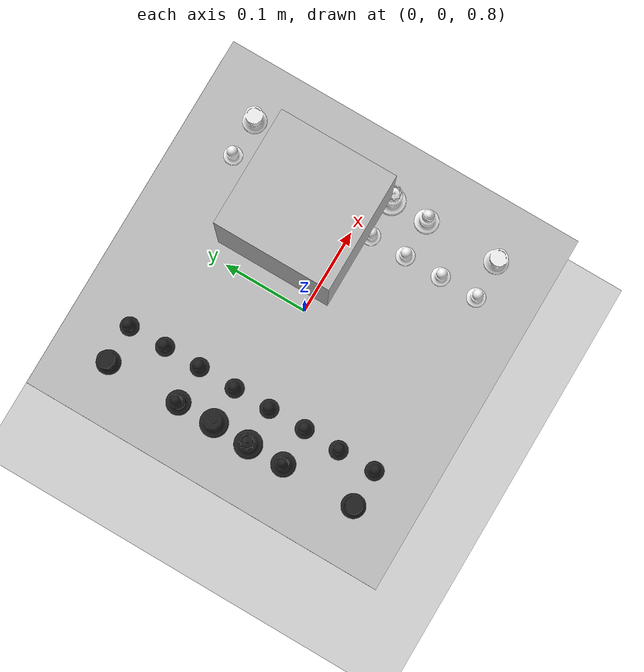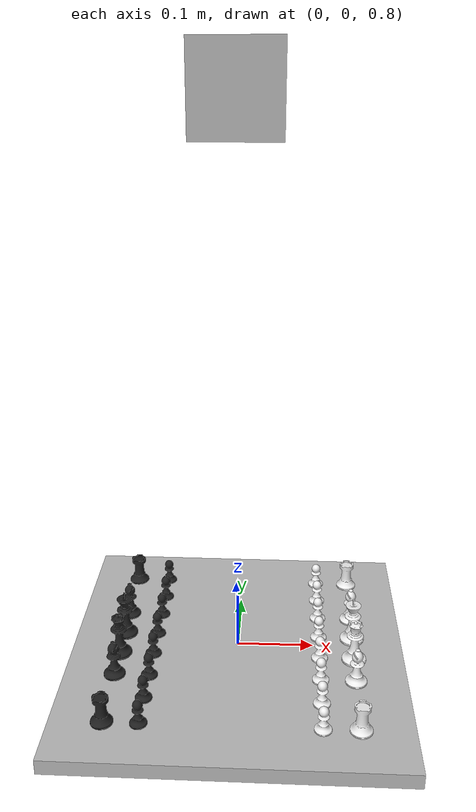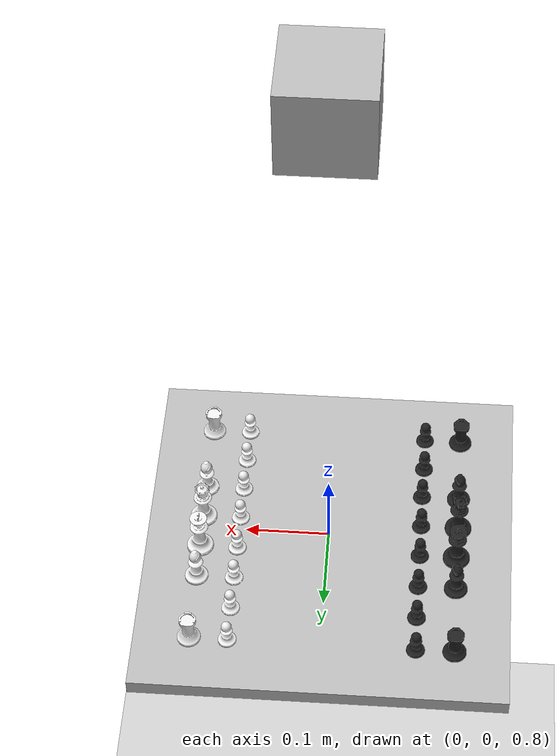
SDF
<sdf version="1.7">
 <world name="default">
  <light name="sun" type="directional">
   <pose>0 0 10 0 -0 0</pose>
   <diffuse>0.8 0.8 0.8 1</diffuse>
   <specular>0.2 0.2 0.2 1</specular>
   <attenuation>
    <range>1000</range>
    <constant>0.9</constant>
    <linear>0.01</linear>
    <quadratic>0.001</quadratic>
   </attenuation>
   <direction>-0.5 0.1 -0.9</direction>
   <spot><inner_angle>0</inner_angle><outer_angle>0</outer_angle><falloff>0</falloff></spot>
  </light>
  <model name="ground_plane">
   <static>1</static>
   <link name="link">
    <collision name="collision">
     <geometry><plane><normal>0 0 1</normal><size>100 100</size></plane></geometry>
     <surface>
      <contact><collide_bitmask>65535</collide_bitmask></contact>
      <friction><ode><mu>100</mu><mu2>50</mu2></ode></friction>
     </surface>
    </collision>
    <visual name="visual">
     <cast_shadows>0</cast_shadows>
     <geometry><plane><normal>0 0 1</normal><size>100 100</size></plane></geometry>
     <material>
      <script><uri>file://media/materials/scripts/gazebo.material</uri><name>Gazebo/Grey</name></script>
     </material>
    </visual>
   </link>
  </model>
  <gravity>0 0 -9.8</gravity>
  <magnetic_field>6e-06 2.3e-05 -4.2e-05</magnetic_field>
  <atmosphere type="adiabatic"/>
  <physics type="ode">
   <max_step_size>0.001</max_step_size>
   <real_time_factor>1</real_time_factor>
   <real_time_update_rate>1000</real_time_update_rate>
  </physics>
  <scene><ambient>0.4 0.4 0.4 1</ambient><background>0.7 0.7 0.7 1</background><shadows>1</shadows></scene>
  <spherical_coordinates>
   <surface_model>EARTH_WGS84</surface_model>
   <latitude_deg>0</latitude_deg>
   <longitude_deg>0</longitude_deg>
   <elevation>0</elevation>
   <heading_deg>0</heading_deg>
  </spherical_coordinates>
  <model name="chess_board">
   <link name="link">
    <inertial>
     <mass>0.5</mass>
     <inertia>
      <ixx>0.166667</ixx>
      <ixy>0</ixy>
      <ixz>0</ixz>
      <iyy>0.166667</iyy>
      <iyz>0</iyz>
      <izz>0.166667</izz>
     </inertia>
    </inertial>
    <visual name="visual">
     <geometry><box><size>0.44 0.44 0.02</size></box></geometry>
     <material>
      <script>
       <name>ChessBoardMaterial</name>
       <uri>model://chess_board/materials/scripts</uri>
       <uri>model://chess_board/materials/textures</uri>
      </script>
     </material>
    </visual>
    <collision name="collision">
     <geometry><box><size>0.44 0.44 0.02</size></box></geometry>
     <surface>
      <friction>
       <ode><mu>1</mu><mu2>1</mu2><fdir1>0 0 0</fdir1><slip1>0</slip1><slip2>0</slip2></ode>
       <torsional>
        <coefficient>1</coefficient>
        <patch_radius>0</patch_radius>
        <surface_radius>0</surface_radius>
        <use_patch_radius>1</use_patch_radius>
        <ode><slip>0</slip></ode>
       </torsional>
      </friction>
      <bounce><restitution_coefficient>0</restitution_coefficient><threshold>1e+06</threshold></bounce>
      <contact>
       <collide_without_contact>0</collide_without_contact>
       <collide_without_contact_bitmask>1</collide_without_contact_bitmask>
       <collide_bitmask>1</collide_bitmask>
       <ode>
        <soft_cfm>0</soft_cfm>
        <soft_erp>0.2</soft_erp>
        <kp>1e+13</kp>
        <kd>1</kd>
        <max_vel>0.01</max_vel>
        <min_depth>0</min_depth>
       </ode>
       <bullet>
        <split_impulse>1</split_impulse>
        <split_impulse_penetration_threshold>-0.01</split_impulse_penetration_threshold>
        <soft_cfm>0</soft_cfm>
        <soft_erp>0.2</soft_erp>
        <kp>1e+13</kp>
        <kd>1</kd>
       </bullet>
      </contact>
     </surface>
    </collision>
   </link>
   <static>0</static>
   <pose>-0.000743 0.000917 0.785005 0 2.4e-05 -3e-05</pose>
  </model>
  <model name="pawn_white">
   <link name="link">
    <inertial>
     <mass>0.1</mass>
     <inertia>
      <ixx>0.166667</ixx>
      <ixy>0</ixy>
      <ixz>0</ixz>
      <iyy>0.166667</iyy>
      <iyz>0</iyz>
      <izz>0.166667</izz>
     </inertia>
    </inertial>
    <visual name="visual">
     <geometry><mesh><uri>model://pawn_white/pawn.stl</uri><scale>0.001 0.001 0.001</scale></mesh></geometry>
     <material>
      <lighting>1</lighting>
      <script><uri>file://media/materials/scripts/gazebo.material</uri><name>Gazebo/White</name></script>
      <shader type="pixel"><normal_map>__default__</normal_map></shader>
      <ambient>1 1 1 1</ambient>
      <diffuse>1 1 1 1</diffuse>
      <specular>0.1 0.1 0.1 1</specular>
      <emissive>0 0 0 1</emissive>
     </material>
    </visual>
    <collision name="collision">
     <geometry><mesh><uri>model://pawn_white/pawn.stl</uri><scale>0.001 0.001 0.001</scale></mesh></geometry>
     <surface>
      <friction>
       <ode><mu>1</mu><mu2>1</mu2><fdir1>0 0 0</fdir1><slip1>0</slip1><slip2>0</slip2></ode>
       <torsional>
        <coefficient>1</coefficient>
        <patch_radius>0</patch_radius>
        <surface_radius>0</surface_radius>
        <use_patch_radius>1</use_patch_radius>
        <ode><slip>0</slip></ode>
       </torsional>
      </friction>
      <bounce><restitution_coefficient>0</restitution_coefficient><threshold>1e+06</threshold></bounce>
      <contact>
       <collide_without_contact>0</collide_without_contact>
       <collide_without_contact_bitmask>1</collide_without_contact_bitmask>
       <collide_bitmask>1</collide_bitmask>
       <ode>
        <soft_cfm>0</soft_cfm>
        <soft_erp>0.2</soft_erp>
        <kp>1e+13</kp>
        <kd>1</kd>
        <max_vel>0.01</max_vel>
        <min_depth>0</min_depth>
       </ode>
       <bullet>
        <split_impulse>1</split_impulse>
        <split_impulse_penetration_threshold>-0.01</split_impulse_penetration_threshold>
        <soft_cfm>0</soft_cfm>
        <soft_erp>0.2</soft_erp>
        <kp>1e+13</kp>
        <kd>1</kd>
       </bullet>
      </contact>
     </surface>
    </collision>
   </link>
   <static>0</static>
   <pose>0.108357 -0.153662 0.795207 0.000231 -9e-05 0.003113</pose>
  </model>
  <model name="pawn_white_0">
   <link name="link">
    <inertial>
     <mass>0.1</mass>
     <inertia>
      <ixx>0.166667</ixx>
      <ixy>0</ixy>
      <ixz>0</ixz>
      <iyy>0.166667</iyy>
      <iyz>0</iyz>
      <izz>0.166667</izz>
     </inertia>
    </inertial>
    <visual name="visual">
     <geometry><mesh><uri>model://pawn_white/pawn.stl</uri><scale>0.001 0.001 0.001</scale></mesh></geometry>
     <material>
      <lighting>1</lighting>
      <script><uri>file://media/materials/scripts/gazebo.material</uri><name>Gazebo/White</name></script>
      <shader type="pixel"><normal_map>__default__</normal_map></shader>
      <ambient>1 1 1 1</ambient>
      <diffuse>1 1 1 1</diffuse>
      <specular>0.1 0.1 0.1 1</specular>
      <emissive>0 0 0 1</emissive>
     </material>
    </visual>
    <collision name="collision">
     <geometry><mesh><uri>model://pawn_white/pawn.stl</uri><scale>0.001 0.001 0.001</scale></mesh></geometry>
     <surface>
      <friction>
       <ode><mu>1</mu><mu2>1</mu2><fdir1>0 0 0</fdir1><slip1>0</slip1><slip2>0</slip2></ode>
       <torsional>
        <coefficient>1</coefficient>
        <patch_radius>0</patch_radius>
        <surface_radius>0</surface_radius>
        <use_patch_radius>1</use_patch_radius>
        <ode><slip>0</slip></ode>
       </torsional>
      </friction>
      <bounce><restitution_coefficient>0</restitution_coefficient><threshold>1e+06</threshold></bounce>
      <contact>
       <collide_without_contact>0</collide_without_contact>
       <collide_without_contact_bitmask>1</collide_without_contact_bitmask>
       <collide_bitmask>1</collide_bitmask>
       <ode>
        <soft_cfm>0</soft_cfm>
        <soft_erp>0.2</soft_erp>
        <kp>1e+13</kp>
        <kd>1</kd>
        <max_vel>0.01</max_vel>
        <min_depth>0</min_depth>
       </ode>
       <bullet>
        <split_impulse>1</split_impulse>
        <split_impulse_penetration_threshold>-0.01</split_impulse_penetration_threshold>
        <soft_cfm>0</soft_cfm>
        <soft_erp>0.2</soft_erp>
        <kp>1e+13</kp>
        <kd>1</kd>
       </bullet>
      </contact>
     </surface>
    </collision>
   </link>
   <static>0</static>
   <pose>0.108486 -0.108727 0.79521 -0.000253 0.000518 0.007603</pose>
  </model>
  <model name="pawn_white_1">
   <link name="link">
    <inertial>
     <mass>0.1</mass>
     <inertia>
      <ixx>0.166667</ixx>
      <ixy>0</ixy>
      <ixz>0</ixz>
      <iyy>0.166667</iyy>
      <iyz>0</iyz>
      <izz>0.166667</izz>
     </inertia>
    </inertial>
    <visual name="visual">
     <geometry><mesh><uri>model://pawn_white/pawn.stl</uri><scale>0.001 0.001 0.001</scale></mesh></geometry>
     <material>
      <lighting>1</lighting>
      <script><uri>file://media/materials/scripts/gazebo.material</uri><name>Gazebo/White</name></script>
      <shader type="pixel"><normal_map>__default__</normal_map></shader>
      <ambient>1 1 1 1</ambient>
      <diffuse>1 1 1 1</diffuse>
      <specular>0.1 0.1 0.1 1</specular>
      <emissive>0 0 0 1</emissive>
     </material>
    </visual>
    <collision name="collision">
     <geometry><mesh><uri>model://pawn_white/pawn.stl</uri><scale>0.001 0.001 0.001</scale></mesh></geometry>
     <surface>
      <friction>
       <ode><mu>1</mu><mu2>1</mu2><fdir1>0 0 0</fdir1><slip1>0</slip1><slip2>0</slip2></ode>
       <torsional>
        <coefficient>1</coefficient>
        <patch_radius>0</patch_radius>
        <surface_radius>0</surface_radius>
        <use_patch_radius>1</use_patch_radius>
        <ode><slip>0</slip></ode>
       </torsional>
      </friction>
      <bounce><restitution_coefficient>0</restitution_coefficient><threshold>1e+06</threshold></bounce>
      <contact>
       <collide_without_contact>0</collide_without_contact>
       <collide_without_contact_bitmask>1</collide_without_contact_bitmask>
       <collide_bitmask>1</collide_bitmask>
       <ode>
        <soft_cfm>0</soft_cfm>
        <soft_erp>0.2</soft_erp>
        <kp>1e+13</kp>
        <kd>1</kd>
        <max_vel>0.01</max_vel>
        <min_depth>0</min_depth>
       </ode>
       <bullet>
        <split_impulse>1</split_impulse>
        <split_impulse_penetration_threshold>-0.01</split_impulse_penetration_threshold>
        <soft_cfm>0</soft_cfm>
        <soft_erp>0.2</soft_erp>
        <kp>1e+13</kp>
        <kd>1</kd>
       </bullet>
      </contact>
     </surface>
    </collision>
   </link>
   <static>0</static>
   <pose>0.108511 -0.064142 0.795222 -0.00043 -0.000387 0.022223</pose>
  </model>
  <model name="pawn_white_2">
   <link name="link">
    <inertial>
     <mass>0.1</mass>
     <inertia>
      <ixx>0.166667</ixx>
      <ixy>0</ixy>
      <ixz>0</ixz>
      <iyy>0.166667</iyy>
      <iyz>0</iyz>
      <izz>0.166667</izz>
     </inertia>
    </inertial>
    <visual name="visual">
     <geometry><mesh><uri>model://pawn_white/pawn.stl</uri><scale>0.001 0.001 0.001</scale></mesh></geometry>
     <material>
      <lighting>1</lighting>
      <script><uri>file://media/materials/scripts/gazebo.material</uri><name>Gazebo/White</name></script>
      <shader type="pixel"><normal_map>__default__</normal_map></shader>
      <ambient>1 1 1 1</ambient>
      <diffuse>1 1 1 1</diffuse>
      <specular>0.1 0.1 0.1 1</specular>
      <emissive>0 0 0 1</emissive>
     </material>
    </visual>
    <collision name="collision">
     <geometry><mesh><uri>model://pawn_white/pawn.stl</uri><scale>0.001 0.001 0.001</scale></mesh></geometry>
     <surface>
      <friction>
       <ode><mu>1</mu><mu2>1</mu2><fdir1>0 0 0</fdir1><slip1>0</slip1><slip2>0</slip2></ode>
       <torsional>
        <coefficient>1</coefficient>
        <patch_radius>0</patch_radius>
        <surface_radius>0</surface_radius>
        <use_patch_radius>1</use_patch_radius>
        <ode><slip>0</slip></ode>
       </torsional>
      </friction>
      <bounce><restitution_coefficient>0</restitution_coefficient><threshold>1e+06</threshold></bounce>
      <contact>
       <collide_without_contact>0</collide_without_contact>
       <collide_without_contact_bitmask>1</collide_without_contact_bitmask>
       <collide_bitmask>1</collide_bitmask>
       <ode>
        <soft_cfm>0</soft_cfm>
        <soft_erp>0.2</soft_erp>
        <kp>1e+13</kp>
        <kd>1</kd>
        <max_vel>0.01</max_vel>
        <min_depth>0</min_depth>
       </ode>
       <bullet>
        <split_impulse>1</split_impulse>
        <split_impulse_penetration_threshold>-0.01</split_impulse_penetration_threshold>
        <soft_cfm>0</soft_cfm>
        <soft_erp>0.2</soft_erp>
        <kp>1e+13</kp>
        <kd>1</kd>
       </bullet>
      </contact>
     </surface>
    </collision>
   </link>
   <static>0</static>
   <pose>0.108561 -0.020482 0.795219 -0.000269 -7.5e-05 0.013174</pose>
  </model>
  <model name="pawn_white_3">
   <link name="link">
    <inertial>
     <mass>0.1</mass>
     <inertia>
      <ixx>0.166667</ixx>
      <ixy>0</ixy>
      <ixz>0</ixz>
      <iyy>0.166667</iyy>
      <iyz>0</iyz>
      <izz>0.166667</izz>
     </inertia>
    </inertial>
    <visual name="visual">
     <geometry><mesh><uri>model://pawn_white/pawn.stl</uri><scale>0.001 0.001 0.001</scale></mesh></geometry>
     <material>
      <lighting>1</lighting>
      <script><uri>file://media/materials/scripts/gazebo.material</uri><name>Gazebo/White</name></script>
      <shader type="pixel"><normal_map>__default__</normal_map></shader>
      <ambient>1 1 1 1</ambient>
      <diffuse>1 1 1 1</diffuse>
      <specular>0.1 0.1 0.1 1</specular>
      <emissive>0 0 0 1</emissive>
     </material>
    </visual>
    <collision name="collision">
     <geometry><mesh><uri>model://pawn_white/pawn.stl</uri><scale>0.001 0.001 0.001</scale></mesh></geometry>
     <surface>
      <friction>
       <ode><mu>1</mu><mu2>1</mu2><fdir1>0 0 0</fdir1><slip1>0</slip1><slip2>0</slip2></ode>
       <torsional>
        <coefficient>1</coefficient>
        <patch_radius>0</patch_radius>
        <surface_radius>0</surface_radius>
        <use_patch_radius>1</use_patch_radius>
        <ode><slip>0</slip></ode>
       </torsional>
      </friction>
      <bounce><restitution_coefficient>0</restitution_coefficient><threshold>1e+06</threshold></bounce>
      <contact>
       <collide_without_contact>0</collide_without_contact>
       <collide_without_contact_bitmask>1</collide_without_contact_bitmask>
       <collide_bitmask>1</collide_bitmask>
       <ode>
        <soft_cfm>0</soft_cfm>
        <soft_erp>0.2</soft_erp>
        <kp>1e+13</kp>
        <kd>1</kd>
        <max_vel>0.01</max_vel>
        <min_depth>0</min_depth>
       </ode>
       <bullet>
        <split_impulse>1</split_impulse>
        <split_impulse_penetration_threshold>-0.01</split_impulse_penetration_threshold>
        <soft_cfm>0</soft_cfm>
        <soft_erp>0.2</soft_erp>
        <kp>1e+13</kp>
        <kd>1</kd>
       </bullet>
      </contact>
     </surface>
    </collision>
   </link>
   <static>0</static>
   <pose>0.108597 0.024215 0.7952 -9.2e-05 0.000234 0.006012</pose>
  </model>
  <model name="pawn_white_4">
   <link name="link">
    <inertial>
     <mass>0.1</mass>
     <inertia>
      <ixx>0.166667</ixx>
      <ixy>0</ixy>
      <ixz>0</ixz>
      <iyy>0.166667</iyy>
      <iyz>0</iyz>
      <izz>0.166667</izz>
     </inertia>
    </inertial>
    <visual name="visual">
     <geometry><mesh><uri>model://pawn_white/pawn.stl</uri><scale>0.001 0.001 0.001</scale></mesh></geometry>
     <material>
      <lighting>1</lighting>
      <script><uri>file://media/materials/scripts/gazebo.material</uri><name>Gazebo/White</name></script>
      <shader type="pixel"><normal_map>__default__</normal_map></shader>
      <ambient>1 1 1 1</ambient>
      <diffuse>1 1 1 1</diffuse>
      <specular>0.1 0.1 0.1 1</specular>
      <emissive>0 0 0 1</emissive>
     </material>
    </visual>
    <collision name="collision">
     <geometry><mesh><uri>model://pawn_white/pawn.stl</uri><scale>0.001 0.001 0.001</scale></mesh></geometry>
     <surface>
      <friction>
       <ode><mu>1</mu><mu2>1</mu2><fdir1>0 0 0</fdir1><slip1>0</slip1><slip2>0</slip2></ode>
       <torsional>
        <coefficient>1</coefficient>
        <patch_radius>0</patch_radius>
        <surface_radius>0</surface_radius>
        <use_patch_radius>1</use_patch_radius>
        <ode><slip>0</slip></ode>
       </torsional>
      </friction>
      <bounce><restitution_coefficient>0</restitution_coefficient><threshold>1e+06</threshold></bounce>
      <contact>
       <collide_without_contact>0</collide_without_contact>
       <collide_without_contact_bitmask>1</collide_without_contact_bitmask>
       <collide_bitmask>1</collide_bitmask>
       <ode>
        <soft_cfm>0</soft_cfm>
        <soft_erp>0.2</soft_erp>
        <kp>1e+13</kp>
        <kd>1</kd>
        <max_vel>0.01</max_vel>
        <min_depth>0</min_depth>
       </ode>
       <bullet>
        <split_impulse>1</split_impulse>
        <split_impulse_penetration_threshold>-0.01</split_impulse_penetration_threshold>
        <soft_cfm>0</soft_cfm>
        <soft_erp>0.2</soft_erp>
        <kp>1e+13</kp>
        <kd>1</kd>
       </bullet>
      </contact>
     </surface>
    </collision>
   </link>
   <static>0</static>
   <pose>0.108616 0.068063 0.795219 -0.000171 -0.001281 8.6e-05</pose>
  </model>
  <model name="pawn_white_5">
   <link name="link">
    <inertial>
     <mass>0.1</mass>
     <inertia>
      <ixx>0.166667</ixx>
      <ixy>0</ixy>
      <ixz>0</ixz>
      <iyy>0.166667</iyy>
      <iyz>0</iyz>
      <izz>0.166667</izz>
     </inertia>
    </inertial>
    <visual name="visual">
     <geometry><mesh><uri>model://pawn_white/pawn.stl</uri><scale>0.001 0.001 0.001</scale></mesh></geometry>
     <material>
      <lighting>1</lighting>
      <script><uri>file://media/materials/scripts/gazebo.material</uri><name>Gazebo/White</name></script>
      <shader type="pixel"><normal_map>__default__</normal_map></shader>
      <ambient>1 1 1 1</ambient>
      <diffuse>1 1 1 1</diffuse>
      <specular>0.1 0.1 0.1 1</specular>
      <emissive>0 0 0 1</emissive>
     </material>
    </visual>
    <collision name="collision">
     <geometry><mesh><uri>model://pawn_white/pawn.stl</uri><scale>0.001 0.001 0.001</scale></mesh></geometry>
     <surface>
      <friction>
       <ode><mu>1</mu><mu2>1</mu2><fdir1>0 0 0</fdir1><slip1>0</slip1><slip2>0</slip2></ode>
       <torsional>
        <coefficient>1</coefficient>
        <patch_radius>0</patch_radius>
        <surface_radius>0</surface_radius>
        <use_patch_radius>1</use_patch_radius>
        <ode><slip>0</slip></ode>
       </torsional>
      </friction>
      <bounce><restitution_coefficient>0</restitution_coefficient><threshold>1e+06</threshold></bounce>
      <contact>
       <collide_without_contact>0</collide_without_contact>
       <collide_without_contact_bitmask>1</collide_without_contact_bitmask>
       <collide_bitmask>1</collide_bitmask>
       <ode>
        <soft_cfm>0</soft_cfm>
        <soft_erp>0.2</soft_erp>
        <kp>1e+13</kp>
        <kd>1</kd>
        <max_vel>0.01</max_vel>
        <min_depth>0</min_depth>
       </ode>
       <bullet>
        <split_impulse>1</split_impulse>
        <split_impulse_penetration_threshold>-0.01</split_impulse_penetration_threshold>
        <soft_cfm>0</soft_cfm>
        <soft_erp>0.2</soft_erp>
        <kp>1e+13</kp>
        <kd>1</kd>
       </bullet>
      </contact>
     </surface>
    </collision>
   </link>
   <static>0</static>
   <pose>0.108731 0.111176 0.795211 0.000464 -0.000278 -0.010669</pose>
  </model>
  <model name="pawn_white_6">
   <link name="link">
    <inertial>
     <mass>0.1</mass>
     <inertia>
      <ixx>0.166667</ixx>
      <ixy>0</ixy>
      <ixz>0</ixz>
      <iyy>0.166667</iyy>
      <iyz>0</iyz>
      <izz>0.166667</izz>
     </inertia>
    </inertial>
    <visual name="visual">
     <geometry><mesh><uri>model://pawn_white/pawn.stl</uri><scale>0.001 0.001 0.001</scale></mesh></geometry>
     <material>
      <lighting>1</lighting>
      <script><uri>file://media/materials/scripts/gazebo.material</uri><name>Gazebo/White</name></script>
      <shader type="pixel"><normal_map>__default__</normal_map></shader>
      <ambient>1 1 1 1</ambient>
      <diffuse>1 1 1 1</diffuse>
      <specular>0.1 0.1 0.1 1</specular>
      <emissive>0 0 0 1</emissive>
     </material>
    </visual>
    <collision name="collision">
     <geometry><mesh><uri>model://pawn_white/pawn.stl</uri><scale>0.001 0.001 0.001</scale></mesh></geometry>
     <surface>
      <friction>
       <ode><mu>1</mu><mu2>1</mu2><fdir1>0 0 0</fdir1><slip1>0</slip1><slip2>0</slip2></ode>
       <torsional>
        <coefficient>1</coefficient>
        <patch_radius>0</patch_radius>
        <surface_radius>0</surface_radius>
        <use_patch_radius>1</use_patch_radius>
        <ode><slip>0</slip></ode>
       </torsional>
      </friction>
      <bounce><restitution_coefficient>0</restitution_coefficient><threshold>1e+06</threshold></bounce>
      <contact>
       <collide_without_contact>0</collide_without_contact>
       <collide_without_contact_bitmask>1</collide_without_contact_bitmask>
       <collide_bitmask>1</collide_bitmask>
       <ode>
        <soft_cfm>0</soft_cfm>
        <soft_erp>0.2</soft_erp>
        <kp>1e+13</kp>
        <kd>1</kd>
        <max_vel>0.01</max_vel>
        <min_depth>0</min_depth>
       </ode>
       <bullet>
        <split_impulse>1</split_impulse>
        <split_impulse_penetration_threshold>-0.01</split_impulse_penetration_threshold>
        <soft_cfm>0</soft_cfm>
        <soft_erp>0.2</soft_erp>
        <kp>1e+13</kp>
        <kd>1</kd>
       </bullet>
      </contact>
     </surface>
    </collision>
   </link>
   <static>0</static>
   <pose>0.108595 0.155332 0.795207 -0.000159 0.000213 -0.018115</pose>
  </model>
  <model name="rook_white">
   <link name="link">
    <inertial>
     <mass>0.1</mass>
     <inertia>
      <ixx>0.166667</ixx>
      <ixy>0</ixy>
      <ixz>0</ixz>
      <iyy>0.166667</iyy>
      <iyz>0</iyz>
      <izz>0.166667</izz>
     </inertia>
    </inertial>
    <visual name="visual">
     <geometry><mesh><uri>model://rook_white/rook.stl</uri><scale>0.001 0.001 0.001</scale></mesh></geometry>
     <material>
      <lighting>1</lighting>
      <script><uri>file://media/materials/scripts/gazebo.material</uri><name>Gazebo/White</name></script>
      <shader type="pixel"><normal_map>__default__</normal_map></shader>
      <ambient>1 1 1 1</ambient>
      <diffuse>1 1 1 1</diffuse>
      <specular>0.1 0.1 0.1 1</specular>
      <emissive>0 0 0 1</emissive>
     </material>
    </visual>
    <collision name="collision">
     <geometry><mesh><uri>model://rook_white/rook.stl</uri><scale>0.001 0.001 0.001</scale></mesh></geometry>
     <surface>
      <friction>
       <ode><mu>1</mu><mu2>1</mu2><fdir1>0 0 0</fdir1><slip1>0</slip1><slip2>0</slip2></ode>
       <torsional>
        <coefficient>1</coefficient>
        <patch_radius>0</patch_radius>
        <surface_radius>0</surface_radius>
        <use_patch_radius>1</use_patch_radius>
        <ode><slip>0</slip></ode>
       </torsional>
      </friction>
      <bounce><restitution_coefficient>0</restitution_coefficient><threshold>1e+06</threshold></bounce>
      <contact>
       <collide_without_contact>0</collide_without_contact>
       <collide_without_contact_bitmask>1</collide_without_contact_bitmask>
       <collide_bitmask>1</collide_bitmask>
       <ode>
        <soft_cfm>0</soft_cfm>
        <soft_erp>0.2</soft_erp>
        <kp>1e+13</kp>
        <kd>1</kd>
        <max_vel>0.01</max_vel>
        <min_depth>0</min_depth>
       </ode>
       <bullet>
        <split_impulse>1</split_impulse>
        <split_impulse_penetration_threshold>-0.01</split_impulse_penetration_threshold>
        <soft_cfm>0</soft_cfm>
        <soft_erp>0.2</soft_erp>
        <kp>1e+13</kp>
        <kd>1</kd>
       </bullet>
      </contact>
     </surface>
    </collision>
   </link>
   <static>0</static>
   <pose>0.153473 -0.152845 0.795149 1.9e-05 -4.4e-05 0.002817</pose>
  </model>
  <model name="rook_white_0">
   <link name="link">
    <inertial>
     <mass>0.1</mass>
     <inertia>
      <ixx>0.166667</ixx>
      <ixy>0</ixy>
      <ixz>0</ixz>
      <iyy>0.166667</iyy>
      <iyz>0</iyz>
      <izz>0.166667</izz>
     </inertia>
    </inertial>
    <visual name="visual">
     <geometry><mesh><uri>model://rook_white/rook.stl</uri><scale>0.001 0.001 0.001</scale></mesh></geometry>
     <material>
      <lighting>1</lighting>
      <script><uri>file://media/materials/scripts/gazebo.material</uri><name>Gazebo/White</name></script>
      <shader type="pixel"><normal_map>__default__</normal_map></shader>
      <ambient>1 1 1 1</ambient>
      <diffuse>1 1 1 1</diffuse>
      <specular>0.1 0.1 0.1 1</specular>
      <emissive>0 0 0 1</emissive>
     </material>
    </visual>
    <collision name="collision">
     <geometry><mesh><uri>model://rook_white/rook.stl</uri><scale>0.001 0.001 0.001</scale></mesh></geometry>
     <surface>
      <friction>
       <ode><mu>1</mu><mu2>1</mu2><fdir1>0 0 0</fdir1><slip1>0</slip1><slip2>0</slip2></ode>
       <torsional>
        <coefficient>1</coefficient>
        <patch_radius>0</patch_radius>
        <surface_radius>0</surface_radius>
        <use_patch_radius>1</use_patch_radius>
        <ode><slip>0</slip></ode>
       </torsional>
      </friction>
      <bounce><restitution_coefficient>0</restitution_coefficient><threshold>1e+06</threshold></bounce>
      <contact>
       <collide_without_contact>0</collide_without_contact>
       <collide_without_contact_bitmask>1</collide_without_contact_bitmask>
       <collide_bitmask>1</collide_bitmask>
       <ode>
        <soft_cfm>0</soft_cfm>
        <soft_erp>0.2</soft_erp>
        <kp>1e+13</kp>
        <kd>1</kd>
        <max_vel>0.01</max_vel>
        <min_depth>0</min_depth>
       </ode>
       <bullet>
        <split_impulse>1</split_impulse>
        <split_impulse_penetration_threshold>-0.01</split_impulse_penetration_threshold>
        <soft_cfm>0</soft_cfm>
        <soft_erp>0.2</soft_erp>
        <kp>1e+13</kp>
        <kd>1</kd>
       </bullet>
      </contact>
     </surface>
    </collision>
   </link>
   <static>0</static>
   <pose>0.153551 0.154399 0.795167 -2.4e-05 -4.3e-05 -0.011534</pose>
  </model>
  <model name="bishop_white">
   <link name="link">
    <inertial>
     <mass>0.1</mass>
     <inertia>
      <ixx>0.166667</ixx>
      <ixy>0</ixy>
      <ixz>0</ixz>
      <iyy>0.166667</iyy>
      <iyz>0</iyz>
      <izz>0.166667</izz>
     </inertia>
    </inertial>
    <visual name="visual">
     <geometry><mesh><uri>model://bishop_white/bishop.stl</uri><scale>0.001 0.001 0.001</scale></mesh></geometry>
     <material>
      <lighting>1</lighting>
      <script><uri>file://media/materials/scripts/gazebo.material</uri><name>Gazebo/White</name></script>
      <shader type="pixel"><normal_map>__default__</normal_map></shader>
      <ambient>1 1 1 1</ambient>
      <diffuse>1 1 1 1</diffuse>
      <specular>0.1 0.1 0.1 1</specular>
      <emissive>0 0 0 1</emissive>
     </material>
    </visual>
    <collision name="collision">
     <geometry><mesh><uri>model://bishop_white/bishop.stl</uri><scale>0.001 0.001 0.001</scale></mesh></geometry>
     <surface>
      <friction>
       <ode><mu>1</mu><mu2>1</mu2><fdir1>0 0 0</fdir1><slip1>0</slip1><slip2>0</slip2></ode>
       <torsional>
        <coefficient>1</coefficient>
        <patch_radius>0</patch_radius>
        <surface_radius>0</surface_radius>
        <use_patch_radius>1</use_patch_radius>
        <ode><slip>0</slip></ode>
       </torsional>
      </friction>
      <bounce><restitution_coefficient>0</restitution_coefficient><threshold>1e+06</threshold></bounce>
      <contact>
       <collide_without_contact>0</collide_without_contact>
       <collide_without_contact_bitmask>1</collide_without_contact_bitmask>
       <collide_bitmask>1</collide_bitmask>
       <ode>
        <soft_cfm>0</soft_cfm>
        <soft_erp>0.2</soft_erp>
        <kp>1e+13</kp>
        <kd>1</kd>
        <max_vel>0.01</max_vel>
        <min_depth>0</min_depth>
       </ode>
       <bullet>
        <split_impulse>1</split_impulse>
        <split_impulse_penetration_threshold>-0.01</split_impulse_penetration_threshold>
        <soft_cfm>0</soft_cfm>
        <soft_erp>0.2</soft_erp>
        <kp>1e+13</kp>
        <kd>1</kd>
       </bullet>
      </contact>
     </surface>
    </collision>
   </link>
   <static>0</static>
   <pose>0.153464 -0.064827 0.795068 2e-05 -0.00068 0.003498</pose>
  </model>
  <model name="bishop_white_0">
   <link name="link">
    <inertial>
     <mass>0.1</mass>
     <inertia>
      <ixx>0.166667</ixx>
      <ixy>0</ixy>
      <ixz>0</ixz>
      <iyy>0.166667</iyy>
      <iyz>0</iyz>
      <izz>0.166667</izz>
     </inertia>
    </inertial>
    <visual name="visual">
     <geometry><mesh><uri>model://bishop_white/bishop.stl</uri><scale>0.001 0.001 0.001</scale></mesh></geometry>
     <material>
      <lighting>1</lighting>
      <script><uri>file://media/materials/scripts/gazebo.material</uri><name>Gazebo/White</name></script>
      <shader type="pixel"><normal_map>__default__</normal_map></shader>
      <ambient>1 1 1 1</ambient>
      <diffuse>1 1 1 1</diffuse>
      <specular>0.1 0.1 0.1 1</specular>
      <emissive>0 0 0 1</emissive>
     </material>
    </visual>
    <collision name="collision">
     <geometry><mesh><uri>model://bishop_white/bishop.stl</uri><scale>0.001 0.001 0.001</scale></mesh></geometry>
     <surface>
      <friction>
       <ode><mu>1</mu><mu2>1</mu2><fdir1>0 0 0</fdir1><slip1>0</slip1><slip2>0</slip2></ode>
       <torsional>
        <coefficient>1</coefficient>
        <patch_radius>0</patch_radius>
        <surface_radius>0</surface_radius>
        <use_patch_radius>1</use_patch_radius>
        <ode><slip>0</slip></ode>
       </torsional>
      </friction>
      <bounce><restitution_coefficient>0</restitution_coefficient><threshold>1e+06</threshold></bounce>
      <contact>
       <collide_without_contact>0</collide_without_contact>
       <collide_without_contact_bitmask>1</collide_without_contact_bitmask>
       <collide_bitmask>1</collide_bitmask>
       <ode>
        <soft_cfm>0</soft_cfm>
        <soft_erp>0.2</soft_erp>
        <kp>1e+13</kp>
        <kd>1</kd>
        <max_vel>0.01</max_vel>
        <min_depth>0</min_depth>
       </ode>
       <bullet>
        <split_impulse>1</split_impulse>
        <split_impulse_penetration_threshold>-0.01</split_impulse_penetration_threshold>
        <soft_cfm>0</soft_cfm>
        <soft_erp>0.2</soft_erp>
        <kp>1e+13</kp>
        <kd>1</kd>
       </bullet>
      </contact>
     </surface>
    </collision>
   </link>
   <static>0</static>
   <pose>0.153461 0.067498 0.795055 8e-05 2.3e-05 -0.00803</pose>
  </model>
  <model name="queen_white">
   <link name="link">
    <inertial>
     <mass>0.1</mass>
     <inertia>
      <ixx>0.166667</ixx>
      <ixy>0</ixy>
      <ixz>0</ixz>
      <iyy>0.166667</iyy>
      <iyz>0</iyz>
      <izz>0.166667</izz>
     </inertia>
    </inertial>
    <visual name="visual">
     <geometry><mesh><uri>model://queen_white/queen.stl</uri><scale>0.001 0.001 0.001</scale></mesh></geometry>
     <material>
      <lighting>1</lighting>
      <script><uri>file://media/materials/scripts/gazebo.material</uri><name>Gazebo/White</name></script>
      <shader type="pixel"><normal_map>__default__</normal_map></shader>
      <ambient>1 1 1 1</ambient>
      <diffuse>1 1 1 1</diffuse>
      <specular>0.1 0.1 0.1 1</specular>
      <emissive>0 0 0 1</emissive>
     </material>
    </visual>
    <collision name="collision">
     <geometry><mesh><uri>model://queen_white/queen.stl</uri><scale>0.001 0.001 0.001</scale></mesh></geometry>
     <surface>
      <friction>
       <ode><mu>1</mu><mu2>1</mu2><fdir1>0 0 0</fdir1><slip1>0</slip1><slip2>0</slip2></ode>
       <torsional>
        <coefficient>1</coefficient>
        <patch_radius>0</patch_radius>
        <surface_radius>0</surface_radius>
        <use_patch_radius>1</use_patch_radius>
        <ode><slip>0</slip></ode>
       </torsional>
      </friction>
      <bounce><restitution_coefficient>0</restitution_coefficient><threshold>1e+06</threshold></bounce>
      <contact>
       <collide_without_contact>0</collide_without_contact>
       <collide_without_contact_bitmask>1</collide_without_contact_bitmask>
       <collide_bitmask>1</collide_bitmask>
       <ode>
        <soft_cfm>0</soft_cfm>
        <soft_erp>0.2</soft_erp>
        <kp>1e+13</kp>
        <kd>1</kd>
        <max_vel>0.01</max_vel>
        <min_depth>0</min_depth>
       </ode>
       <bullet>
        <split_impulse>1</split_impulse>
        <split_impulse_penetration_threshold>-0.01</split_impulse_penetration_threshold>
        <soft_cfm>0</soft_cfm>
        <soft_erp>0.2</soft_erp>
        <kp>1e+13</kp>
        <kd>1</kd>
       </bullet>
      </contact>
     </surface>
    </collision>
   </link>
   <static>0</static>
   <pose>0.153514 -0.020466 0.794913 -1.6e-05 0.000315 -0.002689</pose>
  </model>
  <model name="king_white">
   <link name="link">
    <inertial>
     <mass>0.1</mass>
     <inertia>
      <ixx>0.166667</ixx>
      <ixy>0</ixy>
      <ixz>0</ixz>
      <iyy>0.166667</iyy>
      <iyz>0</iyz>
      <izz>0.166667</izz>
     </inertia>
    </inertial>
    <visual name="visual">
     <geometry><mesh><uri>model://king_white/king.stl</uri><scale>0.001 0.001 0.001</scale></mesh></geometry>
     <material>
      <lighting>1</lighting>
      <script><uri>file://media/materials/scripts/gazebo.material</uri><name>Gazebo/White</name></script>
      <shader type="pixel"><normal_map>__default__</normal_map></shader>
      <ambient>1 1 1 1</ambient>
      <diffuse>1 1 1 1</diffuse>
      <specular>0.1 0.1 0.1 1</specular>
      <emissive>0 0 0 1</emissive>
     </material>
    </visual>
    <collision name="collision">
     <geometry><mesh><uri>model://king_white/king.stl</uri><scale>0.001 0.001 0.001</scale></mesh></geometry>
     <surface>
      <friction>
       <ode><mu>1</mu><mu2>1</mu2><fdir1>0 0 0</fdir1><slip1>0</slip1><slip2>0</slip2></ode>
       <torsional>
        <coefficient>1</coefficient>
        <patch_radius>0</patch_radius>
        <surface_radius>0</surface_radius>
        <use_patch_radius>1</use_patch_radius>
        <ode><slip>0</slip></ode>
       </torsional>
      </friction>
      <bounce><restitution_coefficient>0</restitution_coefficient><threshold>1e+06</threshold></bounce>
      <contact>
       <collide_without_contact>0</collide_without_contact>
       <collide_without_contact_bitmask>1</collide_without_contact_bitmask>
       <collide_bitmask>1</collide_bitmask>
       <ode>
        <soft_cfm>0</soft_cfm>
        <soft_erp>0.2</soft_erp>
        <kp>1e+13</kp>
        <kd>1</kd>
        <max_vel>0.01</max_vel>
        <min_depth>0</min_depth>
       </ode>
       <bullet>
        <split_impulse>1</split_impulse>
        <split_impulse_penetration_threshold>-0.01</split_impulse_penetration_threshold>
        <soft_cfm>0</soft_cfm>
        <soft_erp>0.2</soft_erp>
        <kp>1e+13</kp>
        <kd>1</kd>
       </bullet>
      </contact>
     </surface>
    </collision>
   </link>
   <static>0</static>
   <pose>0.153552 0.023127 0.794695 6e-06 -1.8e-05 1.5719</pose>
  </model>
  <model name="pawn_black">
   <link name="link">
    <inertial>
     <mass>0.1</mass>
     <inertia>
      <ixx>0.166667</ixx>
      <ixy>0</ixy>
      <ixz>0</ixz>
      <iyy>0.166667</iyy>
      <iyz>0</iyz>
      <izz>0.166667</izz>
     </inertia>
    </inertial>
    <visual name="visual">
     <geometry><mesh><uri>model://pawn_black/pawn.stl</uri><scale>0.001 0.001 0.001</scale></mesh></geometry>
     <material>
      <lighting>1</lighting>
      <script><uri>file://media/materials/scripts/gazebo.material</uri><name>Gazebo/Black</name></script>
      <shader type="pixel"><normal_map>__default__</normal_map></shader>
      <ambient>0.3 0.3 0.3 1</ambient>
      <diffuse>0.3 0.3 0.3 1</diffuse>
      <specular>0.1 0.1 0.1 1</specular>
      <emissive>0 0 0 1</emissive>
     </material>
    </visual>
    <collision name="collision">
     <geometry><mesh><uri>model://pawn_black/pawn.stl</uri><scale>0.001 0.001 0.001</scale></mesh></geometry>
     <surface>
      <friction>
       <ode><mu>1</mu><mu2>1</mu2><fdir1>0 0 0</fdir1><slip1>0</slip1><slip2>0</slip2></ode>
       <torsional>
        <coefficient>1</coefficient>
        <patch_radius>0</patch_radius>
        <surface_radius>0</surface_radius>
        <use_patch_radius>1</use_patch_radius>
        <ode><slip>0</slip></ode>
       </torsional>
      </friction>
      <bounce><restitution_coefficient>0</restitution_coefficient><threshold>1e+06</threshold></bounce>
      <contact>
       <collide_without_contact>0</collide_without_contact>
       <collide_without_contact_bitmask>1</collide_without_contact_bitmask>
       <collide_bitmask>1</collide_bitmask>
       <ode>
        <soft_cfm>0</soft_cfm>
        <soft_erp>0.2</soft_erp>
        <kp>1e+13</kp>
        <kd>1</kd>
        <max_vel>0.01</max_vel>
        <min_depth>0</min_depth>
       </ode>
       <bullet>
        <split_impulse>1</split_impulse>
        <split_impulse_penetration_threshold>-0.01</split_impulse_penetration_threshold>
        <soft_cfm>0</soft_cfm>
        <soft_erp>0.2</soft_erp>
        <kp>1e+13</kp>
        <kd>1</kd>
       </bullet>
      </contact>
     </surface>
    </collision>
   </link>
   <static>0</static>
   <pose>-0.111188 -0.153614 0.795213 0.000217 0.0001 0.001653</pose>
  </model>
  <model name="pawn_black_0">
   <link name="link">
    <inertial>
     <mass>0.1</mass>
     <inertia>
      <ixx>0.166667</ixx>
      <ixy>0</ixy>
      <ixz>0</ixz>
      <iyy>0.166667</iyy>
      <iyz>0</iyz>
      <izz>0.166667</izz>
     </inertia>
    </inertial>
    <visual name="visual">
     <geometry><mesh><uri>model://pawn_black/pawn.stl</uri><scale>0.001 0.001 0.001</scale></mesh></geometry>
     <material>
      <lighting>1</lighting>
      <script><uri>file://media/materials/scripts/gazebo.material</uri><name>Gazebo/Black</name></script>
      <shader type="pixel"><normal_map>__default__</normal_map></shader>
      <ambient>0.3 0.3 0.3 1</ambient>
      <diffuse>0.3 0.3 0.3 1</diffuse>
      <specular>0.1 0.1 0.1 1</specular>
      <emissive>0 0 0 1</emissive>
     </material>
    </visual>
    <collision name="collision">
     <geometry><mesh><uri>model://pawn_black/pawn.stl</uri><scale>0.001 0.001 0.001</scale></mesh></geometry>
     <surface>
      <friction>
       <ode><mu>1</mu><mu2>1</mu2><fdir1>0 0 0</fdir1><slip1>0</slip1><slip2>0</slip2></ode>
       <torsional>
        <coefficient>1</coefficient>
        <patch_radius>0</patch_radius>
        <surface_radius>0</surface_radius>
        <use_patch_radius>1</use_patch_radius>
        <ode><slip>0</slip></ode>
       </torsional>
      </friction>
      <bounce><restitution_coefficient>0</restitution_coefficient><threshold>1e+06</threshold></bounce>
      <contact>
       <collide_without_contact>0</collide_without_contact>
       <collide_without_contact_bitmask>1</collide_without_contact_bitmask>
       <collide_bitmask>1</collide_bitmask>
       <ode>
        <soft_cfm>0</soft_cfm>
        <soft_erp>0.2</soft_erp>
        <kp>1e+13</kp>
        <kd>1</kd>
        <max_vel>0.01</max_vel>
        <min_depth>0</min_depth>
       </ode>
       <bullet>
        <split_impulse>1</split_impulse>
        <split_impulse_penetration_threshold>-0.01</split_impulse_penetration_threshold>
        <soft_cfm>0</soft_cfm>
        <soft_erp>0.2</soft_erp>
        <kp>1e+13</kp>
        <kd>1</kd>
       </bullet>
      </contact>
     </surface>
    </collision>
   </link>
   <static>0</static>
   <pose>-0.111529 -0.108762 0.795217 0.000481 0.000399 0.001416</pose>
  </model>
  <model name="pawn_black_1">
   <link name="link">
    <inertial>
     <mass>0.1</mass>
     <inertia>
      <ixx>0.166667</ixx>
      <ixy>0</ixy>
      <ixz>0</ixz>
      <iyy>0.166667</iyy>
      <iyz>0</iyz>
      <izz>0.166667</izz>
     </inertia>
    </inertial>
    <visual name="visual">
     <geometry><mesh><uri>model://pawn_black/pawn.stl</uri><scale>0.001 0.001 0.001</scale></mesh></geometry>
     <material>
      <lighting>1</lighting>
      <script><uri>file://media/materials/scripts/gazebo.material</uri><name>Gazebo/Black</name></script>
      <shader type="pixel"><normal_map>__default__</normal_map></shader>
      <ambient>0.3 0.3 0.3 1</ambient>
      <diffuse>0.3 0.3 0.3 1</diffuse>
      <specular>0.1 0.1 0.1 1</specular>
      <emissive>0 0 0 1</emissive>
     </material>
    </visual>
    <collision name="collision">
     <geometry><mesh><uri>model://pawn_black/pawn.stl</uri><scale>0.001 0.001 0.001</scale></mesh></geometry>
     <surface>
      <friction>
       <ode><mu>1</mu><mu2>1</mu2><fdir1>0 0 0</fdir1><slip1>0</slip1><slip2>0</slip2></ode>
       <torsional>
        <coefficient>1</coefficient>
        <patch_radius>0</patch_radius>
        <surface_radius>0</surface_radius>
        <use_patch_radius>1</use_patch_radius>
        <ode><slip>0</slip></ode>
       </torsional>
      </friction>
      <bounce><restitution_coefficient>0</restitution_coefficient><threshold>1e+06</threshold></bounce>
      <contact>
       <collide_without_contact>0</collide_without_contact>
       <collide_without_contact_bitmask>1</collide_without_contact_bitmask>
       <collide_bitmask>1</collide_bitmask>
       <ode>
        <soft_cfm>0</soft_cfm>
        <soft_erp>0.2</soft_erp>
        <kp>1e+13</kp>
        <kd>1</kd>
        <max_vel>0.01</max_vel>
        <min_depth>0</min_depth>
       </ode>
       <bullet>
        <split_impulse>1</split_impulse>
        <split_impulse_penetration_threshold>-0.01</split_impulse_penetration_threshold>
        <soft_cfm>0</soft_cfm>
        <soft_erp>0.2</soft_erp>
        <kp>1e+13</kp>
        <kd>1</kd>
       </bullet>
      </contact>
     </surface>
    </collision>
   </link>
   <static>0</static>
   <pose>-0.11055 -0.065455 0.795218 0.000372 -0.000639 0.000222</pose>
  </model>
  <model name="pawn_black_2">
   <link name="link">
    <inertial>
     <mass>0.1</mass>
     <inertia>
      <ixx>0.166667</ixx>
      <ixy>0</ixy>
      <ixz>0</ixz>
      <iyy>0.166667</iyy>
      <iyz>0</iyz>
      <izz>0.166667</izz>
     </inertia>
    </inertial>
    <visual name="visual">
     <geometry><mesh><uri>model://pawn_black/pawn.stl</uri><scale>0.001 0.001 0.001</scale></mesh></geometry>
     <material>
      <lighting>1</lighting>
      <script><uri>file://media/materials/scripts/gazebo.material</uri><name>Gazebo/Black</name></script>
      <shader type="pixel"><normal_map>__default__</normal_map></shader>
      <ambient>0.3 0.3 0.3 1</ambient>
      <diffuse>0.3 0.3 0.3 1</diffuse>
      <specular>0.1 0.1 0.1 1</specular>
      <emissive>0 0 0 1</emissive>
     </material>
    </visual>
    <collision name="collision">
     <geometry><mesh><uri>model://pawn_black/pawn.stl</uri><scale>0.001 0.001 0.001</scale></mesh></geometry>
     <surface>
      <friction>
       <ode><mu>1</mu><mu2>1</mu2><fdir1>0 0 0</fdir1><slip1>0</slip1><slip2>0</slip2></ode>
       <torsional>
        <coefficient>1</coefficient>
        <patch_radius>0</patch_radius>
        <surface_radius>0</surface_radius>
        <use_patch_radius>1</use_patch_radius>
        <ode><slip>0</slip></ode>
       </torsional>
      </friction>
      <bounce><restitution_coefficient>0</restitution_coefficient><threshold>1e+06</threshold></bounce>
      <contact>
       <collide_without_contact>0</collide_without_contact>
       <collide_without_contact_bitmask>1</collide_without_contact_bitmask>
       <collide_bitmask>1</collide_bitmask>
       <ode>
        <soft_cfm>0</soft_cfm>
        <soft_erp>0.2</soft_erp>
        <kp>1e+13</kp>
        <kd>1</kd>
        <max_vel>0.01</max_vel>
        <min_depth>0</min_depth>
       </ode>
       <bullet>
        <split_impulse>1</split_impulse>
        <split_impulse_penetration_threshold>-0.01</split_impulse_penetration_threshold>
        <soft_cfm>0</soft_cfm>
        <soft_erp>0.2</soft_erp>
        <kp>1e+13</kp>
        <kd>1</kd>
       </bullet>
      </contact>
     </surface>
    </collision>
   </link>
   <static>0</static>
   <pose>-0.111116 -0.021215 0.795209 0.000124 -9.6e-05 5.8e-05</pose>
  </model>
  <model name="pawn_black_3">
   <link name="link">
    <inertial>
     <mass>0.1</mass>
     <inertia>
      <ixx>0.166667</ixx>
      <ixy>0</ixy>
      <ixz>0</ixz>
      <iyy>0.166667</iyy>
      <iyz>0</iyz>
      <izz>0.166667</izz>
     </inertia>
    </inertial>
    <visual name="visual">
     <geometry><mesh><uri>model://pawn_black/pawn.stl</uri><scale>0.001 0.001 0.001</scale></mesh></geometry>
     <material>
      <lighting>1</lighting>
      <script><uri>file://media/materials/scripts/gazebo.material</uri><name>Gazebo/Black</name></script>
      <shader type="pixel"><normal_map>__default__</normal_map></shader>
      <ambient>0.3 0.3 0.3 1</ambient>
      <diffuse>0.3 0.3 0.3 1</diffuse>
      <specular>0.1 0.1 0.1 1</specular>
      <emissive>0 0 0 1</emissive>
     </material>
    </visual>
    <collision name="collision">
     <geometry><mesh><uri>model://pawn_black/pawn.stl</uri><scale>0.001 0.001 0.001</scale></mesh></geometry>
     <surface>
      <friction>
       <ode><mu>1</mu><mu2>1</mu2><fdir1>0 0 0</fdir1><slip1>0</slip1><slip2>0</slip2></ode>
       <torsional>
        <coefficient>1</coefficient>
        <patch_radius>0</patch_radius>
        <surface_radius>0</surface_radius>
        <use_patch_radius>1</use_patch_radius>
        <ode><slip>0</slip></ode>
       </torsional>
      </friction>
      <bounce><restitution_coefficient>0</restitution_coefficient><threshold>1e+06</threshold></bounce>
      <contact>
       <collide_without_contact>0</collide_without_contact>
       <collide_without_contact_bitmask>1</collide_without_contact_bitmask>
       <collide_bitmask>1</collide_bitmask>
       <ode>
        <soft_cfm>0</soft_cfm>
        <soft_erp>0.2</soft_erp>
        <kp>1e+13</kp>
        <kd>1</kd>
        <max_vel>0.01</max_vel>
        <min_depth>0</min_depth>
       </ode>
       <bullet>
        <split_impulse>1</split_impulse>
        <split_impulse_penetration_threshold>-0.01</split_impulse_penetration_threshold>
        <soft_cfm>0</soft_cfm>
        <soft_erp>0.2</soft_erp>
        <kp>1e+13</kp>
        <kd>1</kd>
       </bullet>
      </contact>
     </surface>
    </collision>
   </link>
   <static>0</static>
   <pose>-0.111094 0.022614 0.795213 0.000222 -7.5e-05 4.2e-05</pose>
  </model>
  <model name="pawn_black_4">
   <link name="link">
    <inertial>
     <mass>0.1</mass>
     <inertia>
      <ixx>0.166667</ixx>
      <ixy>0</ixy>
      <ixz>0</ixz>
      <iyy>0.166667</iyy>
      <iyz>0</iyz>
      <izz>0.166667</izz>
     </inertia>
    </inertial>
    <visual name="visual">
     <geometry><mesh><uri>model://pawn_black/pawn.stl</uri><scale>0.001 0.001 0.001</scale></mesh></geometry>
     <material>
      <lighting>1</lighting>
      <script><uri>file://media/materials/scripts/gazebo.material</uri><name>Gazebo/Black</name></script>
      <shader type="pixel"><normal_map>__default__</normal_map></shader>
      <ambient>0.3 0.3 0.3 1</ambient>
      <diffuse>0.3 0.3 0.3 1</diffuse>
      <specular>0.1 0.1 0.1 1</specular>
      <emissive>0 0 0 1</emissive>
     </material>
    </visual>
    <collision name="collision">
     <geometry><mesh><uri>model://pawn_black/pawn.stl</uri><scale>0.001 0.001 0.001</scale></mesh></geometry>
     <surface>
      <friction>
       <ode><mu>1</mu><mu2>1</mu2><fdir1>0 0 0</fdir1><slip1>0</slip1><slip2>0</slip2></ode>
       <torsional>
        <coefficient>1</coefficient>
        <patch_radius>0</patch_radius>
        <surface_radius>0</surface_radius>
        <use_patch_radius>1</use_patch_radius>
        <ode><slip>0</slip></ode>
       </torsional>
      </friction>
      <bounce><restitution_coefficient>0</restitution_coefficient><threshold>1e+06</threshold></bounce>
      <contact>
       <collide_without_contact>0</collide_without_contact>
       <collide_without_contact_bitmask>1</collide_without_contact_bitmask>
       <collide_bitmask>1</collide_bitmask>
       <ode>
        <soft_cfm>0</soft_cfm>
        <soft_erp>0.2</soft_erp>
        <kp>1e+13</kp>
        <kd>1</kd>
        <max_vel>0.01</max_vel>
        <min_depth>0</min_depth>
       </ode>
       <bullet>
        <split_impulse>1</split_impulse>
        <split_impulse_penetration_threshold>-0.01</split_impulse_penetration_threshold>
        <soft_cfm>0</soft_cfm>
        <soft_erp>0.2</soft_erp>
        <kp>1e+13</kp>
        <kd>1</kd>
       </bullet>
      </contact>
     </surface>
    </collision>
   </link>
   <static>0</static>
   <pose>-0.110611 0.067324 0.795213 -0.000183 -0.000187 -0.000241</pose>
  </model>
  <model name="pawn_black_5">
   <link name="link">
    <inertial>
     <mass>0.1</mass>
     <inertia>
      <ixx>0.166667</ixx>
      <ixy>0</ixy>
      <ixz>0</ixz>
      <iyy>0.166667</iyy>
      <iyz>0</iyz>
      <izz>0.166667</izz>
     </inertia>
    </inertial>
    <visual name="visual">
     <geometry><mesh><uri>model://pawn_black/pawn.stl</uri><scale>0.001 0.001 0.001</scale></mesh></geometry>
     <material>
      <lighting>1</lighting>
      <script><uri>file://media/materials/scripts/gazebo.material</uri><name>Gazebo/Black</name></script>
      <shader type="pixel"><normal_map>__default__</normal_map></shader>
      <ambient>0.3 0.3 0.3 1</ambient>
      <diffuse>0.3 0.3 0.3 1</diffuse>
      <specular>0.1 0.1 0.1 1</specular>
      <emissive>0 0 0 1</emissive>
     </material>
    </visual>
    <collision name="collision">
     <geometry><mesh><uri>model://pawn_black/pawn.stl</uri><scale>0.001 0.001 0.001</scale></mesh></geometry>
     <surface>
      <friction>
       <ode><mu>1</mu><mu2>1</mu2><fdir1>0 0 0</fdir1><slip1>0</slip1><slip2>0</slip2></ode>
       <torsional>
        <coefficient>1</coefficient>
        <patch_radius>0</patch_radius>
        <surface_radius>0</surface_radius>
        <use_patch_radius>1</use_patch_radius>
        <ode><slip>0</slip></ode>
       </torsional>
      </friction>
      <bounce><restitution_coefficient>0</restitution_coefficient><threshold>1e+06</threshold></bounce>
      <contact>
       <collide_without_contact>0</collide_without_contact>
       <collide_without_contact_bitmask>1</collide_without_contact_bitmask>
       <collide_bitmask>1</collide_bitmask>
       <ode>
        <soft_cfm>0</soft_cfm>
        <soft_erp>0.2</soft_erp>
        <kp>1e+13</kp>
        <kd>1</kd>
        <max_vel>0.01</max_vel>
        <min_depth>0</min_depth>
       </ode>
       <bullet>
        <split_impulse>1</split_impulse>
        <split_impulse_penetration_threshold>-0.01</split_impulse_penetration_threshold>
        <soft_cfm>0</soft_cfm>
        <soft_erp>0.2</soft_erp>
        <kp>1e+13</kp>
        <kd>1</kd>
       </bullet>
      </contact>
     </surface>
    </collision>
   </link>
   <static>0</static>
   <pose>-0.110617 0.111126 0.795209 -0.000274 -3.3e-05 -0.000156</pose>
  </model>
  <model name="pawn_black_6">
   <link name="link">
    <inertial>
     <mass>0.1</mass>
     <inertia>
      <ixx>0.166667</ixx>
      <ixy>0</ixy>
      <ixz>0</ixz>
      <iyy>0.166667</iyy>
      <iyz>0</iyz>
      <izz>0.166667</izz>
     </inertia>
    </inertial>
    <visual name="visual">
     <geometry><mesh><uri>model://pawn_black/pawn.stl</uri><scale>0.001 0.001 0.001</scale></mesh></geometry>
     <material>
      <lighting>1</lighting>
      <script><uri>file://media/materials/scripts/gazebo.material</uri><name>Gazebo/Black</name></script>
      <shader type="pixel"><normal_map>__default__</normal_map></shader>
      <ambient>0.3 0.3 0.3 1</ambient>
      <diffuse>0.3 0.3 0.3 1</diffuse>
      <specular>0.1 0.1 0.1 1</specular>
      <emissive>0 0 0 1</emissive>
     </material>
    </visual>
    <collision name="collision">
     <geometry><mesh><uri>model://pawn_black/pawn.stl</uri><scale>0.001 0.001 0.001</scale></mesh></geometry>
     <surface>
      <friction>
       <ode><mu>1</mu><mu2>1</mu2><fdir1>0 0 0</fdir1><slip1>0</slip1><slip2>0</slip2></ode>
       <torsional>
        <coefficient>1</coefficient>
        <patch_radius>0</patch_radius>
        <surface_radius>0</surface_radius>
        <use_patch_radius>1</use_patch_radius>
        <ode><slip>0</slip></ode>
       </torsional>
      </friction>
      <bounce><restitution_coefficient>0</restitution_coefficient><threshold>1e+06</threshold></bounce>
      <contact>
       <collide_without_contact>0</collide_without_contact>
       <collide_without_contact_bitmask>1</collide_without_contact_bitmask>
       <collide_bitmask>1</collide_bitmask>
       <ode>
        <soft_cfm>0</soft_cfm>
        <soft_erp>0.2</soft_erp>
        <kp>1e+13</kp>
        <kd>1</kd>
        <max_vel>0.01</max_vel>
        <min_depth>0</min_depth>
       </ode>
       <bullet>
        <split_impulse>1</split_impulse>
        <split_impulse_penetration_threshold>-0.01</split_impulse_penetration_threshold>
        <soft_cfm>0</soft_cfm>
        <soft_erp>0.2</soft_erp>
        <kp>1e+13</kp>
        <kd>1</kd>
       </bullet>
      </contact>
     </surface>
    </collision>
   </link>
   <static>0</static>
   <pose>-0.111055 0.15584 0.795216 -0.000552 0.000186 -0.000349</pose>
  </model>
  <model name="rook_black">
   <link name="link">
    <inertial>
     <mass>0.1</mass>
     <inertia>
      <ixx>0.166667</ixx>
      <ixy>0</ixy>
      <ixz>0</ixz>
      <iyy>0.166667</iyy>
      <iyz>0</iyz>
      <izz>0.166667</izz>
     </inertia>
    </inertial>
    <visual name="visual">
     <geometry><mesh><uri>model://rook_black/rook.stl</uri><scale>0.001 0.001 0.001</scale></mesh></geometry>
     <material>
      <lighting>1</lighting>
      <script><uri>file://media/materials/scripts/gazebo.material</uri><name>Gazebo/Black</name></script>
      <shader type="pixel"><normal_map>__default__</normal_map></shader>
      <ambient>0.3 0.3 0.3 1</ambient>
      <diffuse>0.3 0.3 0.3 1</diffuse>
      <specular>0.1 0.1 0.1 1</specular>
      <emissive>0 0 0 1</emissive>
     </material>
    </visual>
    <collision name="collision">
     <geometry><mesh><uri>model://rook_black/rook.stl</uri><scale>0.001 0.001 0.001</scale></mesh></geometry>
     <surface>
      <friction>
       <ode><mu>1</mu><mu2>1</mu2><fdir1>0 0 0</fdir1><slip1>0</slip1><slip2>0</slip2></ode>
       <torsional>
        <coefficient>1</coefficient>
        <patch_radius>0</patch_radius>
        <surface_radius>0</surface_radius>
        <use_patch_radius>1</use_patch_radius>
        <ode><slip>0</slip></ode>
       </torsional>
      </friction>
      <bounce><restitution_coefficient>0</restitution_coefficient><threshold>1e+06</threshold></bounce>
      <contact>
       <collide_without_contact>0</collide_without_contact>
       <collide_without_contact_bitmask>1</collide_without_contact_bitmask>
       <collide_bitmask>1</collide_bitmask>
       <ode>
        <soft_cfm>0</soft_cfm>
        <soft_erp>0.2</soft_erp>
        <kp>1e+13</kp>
        <kd>1</kd>
        <max_vel>0.01</max_vel>
        <min_depth>0</min_depth>
       </ode>
       <bullet>
        <split_impulse>1</split_impulse>
        <split_impulse_penetration_threshold>-0.01</split_impulse_penetration_threshold>
        <soft_cfm>0</soft_cfm>
        <soft_erp>0.2</soft_erp>
        <kp>1e+13</kp>
        <kd>1</kd>
       </bullet>
      </contact>
     </surface>
    </collision>
   </link>
   <static>0</static>
   <pose>-0.155325 -0.15305 0.795165 5.4e-05 -0.000142 -0.000157</pose>
  </model>
  <model name="rook_black_0">
   <link name="link">
    <inertial>
     <mass>0.1</mass>
     <inertia>
      <ixx>0.166667</ixx>
      <ixy>0</ixy>
      <ixz>0</ixz>
      <iyy>0.166667</iyy>
      <iyz>0</iyz>
      <izz>0.166667</izz>
     </inertia>
    </inertial>
    <visual name="visual">
     <geometry><mesh><uri>model://rook_black/rook.stl</uri><scale>0.001 0.001 0.001</scale></mesh></geometry>
     <material>
      <lighting>1</lighting>
      <script><uri>file://media/materials/scripts/gazebo.material</uri><name>Gazebo/Black</name></script>
      <shader type="pixel"><normal_map>__default__</normal_map></shader>
      <ambient>0.3 0.3 0.3 1</ambient>
      <diffuse>0.3 0.3 0.3 1</diffuse>
      <specular>0.1 0.1 0.1 1</specular>
      <emissive>0 0 0 1</emissive>
     </material>
    </visual>
    <collision name="collision">
     <geometry><mesh><uri>model://rook_black/rook.stl</uri><scale>0.001 0.001 0.001</scale></mesh></geometry>
     <surface>
      <friction>
       <ode><mu>1</mu><mu2>1</mu2><fdir1>0 0 0</fdir1><slip1>0</slip1><slip2>0</slip2></ode>
       <torsional>
        <coefficient>1</coefficient>
        <patch_radius>0</patch_radius>
        <surface_radius>0</surface_radius>
        <use_patch_radius>1</use_patch_radius>
        <ode><slip>0</slip></ode>
       </torsional>
      </friction>
      <bounce><restitution_coefficient>0</restitution_coefficient><threshold>1e+06</threshold></bounce>
      <contact>
       <collide_without_contact>0</collide_without_contact>
       <collide_without_contact_bitmask>1</collide_without_contact_bitmask>
       <collide_bitmask>1</collide_bitmask>
       <ode>
        <soft_cfm>0</soft_cfm>
        <soft_erp>0.2</soft_erp>
        <kp>1e+13</kp>
        <kd>1</kd>
        <max_vel>0.01</max_vel>
        <min_depth>0</min_depth>
       </ode>
       <bullet>
        <split_impulse>1</split_impulse>
        <split_impulse_penetration_threshold>-0.01</split_impulse_penetration_threshold>
        <soft_cfm>0</soft_cfm>
        <soft_erp>0.2</soft_erp>
        <kp>1e+13</kp>
        <kd>1</kd>
       </bullet>
      </contact>
     </surface>
    </collision>
   </link>
   <static>0</static>
   <pose>-0.156338 0.155444 0.795176 5.4e-05 -1.4e-05 -0.000133</pose>
  </model>
  <model name="bishop_black">
   <link name="link">
    <inertial>
     <mass>0.1</mass>
     <inertia>
      <ixx>0.166667</ixx>
      <ixy>0</ixy>
      <ixz>0</ixz>
      <iyy>0.166667</iyy>
      <iyz>0</iyz>
      <izz>0.166667</izz>
     </inertia>
    </inertial>
    <visual name="visual">
     <geometry><mesh><uri>model://bishop_black/bishop.stl</uri><scale>0.001 0.001 0.001</scale></mesh></geometry>
     <material>
      <lighting>1</lighting>
      <script><uri>file://media/materials/scripts/gazebo.material</uri><name>Gazebo/Black</name></script>
      <shader type="pixel"><normal_map>__default__</normal_map></shader>
      <ambient>0.3 0.3 0.3 1</ambient>
      <diffuse>0.3 0.3 0.3 1</diffuse>
      <specular>0.1 0.1 0.1 1</specular>
      <emissive>0 0 0 1</emissive>
     </material>
    </visual>
    <collision name="collision">
     <geometry><mesh><uri>model://bishop_black/bishop.stl</uri><scale>0.001 0.001 0.001</scale></mesh></geometry>
     <surface>
      <friction>
       <ode><mu>1</mu><mu2>1</mu2><fdir1>0 0 0</fdir1><slip1>0</slip1><slip2>0</slip2></ode>
       <torsional>
        <coefficient>1</coefficient>
        <patch_radius>0</patch_radius>
        <surface_radius>0</surface_radius>
        <use_patch_radius>1</use_patch_radius>
        <ode><slip>0</slip></ode>
       </torsional>
      </friction>
      <bounce><restitution_coefficient>0</restitution_coefficient><threshold>1e+06</threshold></bounce>
      <contact>
       <collide_without_contact>0</collide_without_contact>
       <collide_without_contact_bitmask>1</collide_without_contact_bitmask>
       <collide_bitmask>1</collide_bitmask>
       <ode>
        <soft_cfm>0</soft_cfm>
        <soft_erp>0.2</soft_erp>
        <kp>1e+13</kp>
        <kd>1</kd>
        <max_vel>0.01</max_vel>
        <min_depth>0</min_depth>
       </ode>
       <bullet>
        <split_impulse>1</split_impulse>
        <split_impulse_penetration_threshold>-0.01</split_impulse_penetration_threshold>
        <soft_cfm>0</soft_cfm>
        <soft_erp>0.2</soft_erp>
        <kp>1e+13</kp>
        <kd>1</kd>
       </bullet>
      </contact>
     </surface>
    </collision>
   </link>
   <static>0</static>
   <pose>-0.155381 -0.065007 0.795079 0.000824 -0.000292 3.14131</pose>
  </model>
  <model name="bishop_black_0">
   <link name="link">
    <inertial>
     <mass>0.1</mass>
     <inertia>
      <ixx>0.166667</ixx>
      <ixy>0</ixy>
      <ixz>0</ixz>
      <iyy>0.166667</iyy>
      <iyz>0</iyz>
      <izz>0.166667</izz>
     </inertia>
    </inertial>
    <visual name="visual">
     <geometry><mesh><uri>model://bishop_black/bishop.stl</uri><scale>0.001 0.001 0.001</scale></mesh></geometry>
     <material>
      <lighting>1</lighting>
      <script><uri>file://media/materials/scripts/gazebo.material</uri><name>Gazebo/Black</name></script>
      <shader type="pixel"><normal_map>__default__</normal_map></shader>
      <ambient>0.3 0.3 0.3 1</ambient>
      <diffuse>0.3 0.3 0.3 1</diffuse>
      <specular>0.1 0.1 0.1 1</specular>
      <emissive>0 0 0 1</emissive>
     </material>
    </visual>
    <collision name="collision">
     <geometry><mesh><uri>model://bishop_black/bishop.stl</uri><scale>0.001 0.001 0.001</scale></mesh></geometry>
     <surface>
      <friction>
       <ode><mu>1</mu><mu2>1</mu2><fdir1>0 0 0</fdir1><slip1>0</slip1><slip2>0</slip2></ode>
       <torsional>
        <coefficient>1</coefficient>
        <patch_radius>0</patch_radius>
        <surface_radius>0</surface_radius>
        <use_patch_radius>1</use_patch_radius>
        <ode><slip>0</slip></ode>
       </torsional>
      </friction>
      <bounce><restitution_coefficient>0</restitution_coefficient><threshold>1e+06</threshold></bounce>
      <contact>
       <collide_without_contact>0</collide_without_contact>
       <collide_without_contact_bitmask>1</collide_without_contact_bitmask>
       <collide_bitmask>1</collide_bitmask>
       <ode>
        <soft_cfm>0</soft_cfm>
        <soft_erp>0.2</soft_erp>
        <kp>1e+13</kp>
        <kd>1</kd>
        <max_vel>0.01</max_vel>
        <min_depth>0</min_depth>
       </ode>
       <bullet>
        <split_impulse>1</split_impulse>
        <split_impulse_penetration_threshold>-0.01</split_impulse_penetration_threshold>
        <soft_cfm>0</soft_cfm>
        <soft_erp>0.2</soft_erp>
        <kp>1e+13</kp>
        <kd>1</kd>
       </bullet>
      </contact>
     </surface>
    </collision>
   </link>
   <static>0</static>
   <pose>-0.15546 0.067286 0.795073 -0.000374 -0.000201 3.1414</pose>
  </model>
  <model name="queen_black">
   <link name="link">
    <inertial>
     <mass>0.1</mass>
     <inertia>
      <ixx>0.166667</ixx>
      <ixy>0</ixy>
      <ixz>0</ixz>
      <iyy>0.166667</iyy>
      <iyz>0</iyz>
      <izz>0.166667</izz>
     </inertia>
    </inertial>
    <visual name="visual">
     <geometry><mesh><uri>model://queen_black/queen.stl</uri><scale>0.001 0.001 0.001</scale></mesh></geometry>
     <material>
      <lighting>1</lighting>
      <script><uri>file://media/materials/scripts/gazebo.material</uri><name>Gazebo/Black</name></script>
      <shader type="pixel"><normal_map>__default__</normal_map></shader>
      <ambient>0.3 0.3 0.3 1</ambient>
      <diffuse>0.3 0.3 0.3 1</diffuse>
      <specular>0.1 0.1 0.1 1</specular>
      <emissive>0 0 0 1</emissive>
     </material>
    </visual>
    <collision name="collision">
     <geometry><mesh><uri>model://queen_black/queen.stl</uri><scale>0.001 0.001 0.001</scale></mesh></geometry>
     <surface>
      <friction>
       <ode><mu>1</mu><mu2>1</mu2><fdir1>0 0 0</fdir1><slip1>0</slip1><slip2>0</slip2></ode>
       <torsional>
        <coefficient>1</coefficient>
        <patch_radius>0</patch_radius>
        <surface_radius>0</surface_radius>
        <use_patch_radius>1</use_patch_radius>
        <ode><slip>0</slip></ode>
       </torsional>
      </friction>
      <bounce><restitution_coefficient>0</restitution_coefficient><threshold>1e+06</threshold></bounce>
      <contact>
       <collide_without_contact>0</collide_without_contact>
       <collide_without_contact_bitmask>1</collide_without_contact_bitmask>
       <collide_bitmask>1</collide_bitmask>
       <ode>
        <soft_cfm>0</soft_cfm>
        <soft_erp>0.2</soft_erp>
        <kp>1e+13</kp>
        <kd>1</kd>
        <max_vel>0.01</max_vel>
        <min_depth>0</min_depth>
       </ode>
       <bullet>
        <split_impulse>1</split_impulse>
        <split_impulse_penetration_threshold>-0.01</split_impulse_penetration_threshold>
        <soft_cfm>0</soft_cfm>
        <soft_erp>0.2</soft_erp>
        <kp>1e+13</kp>
        <kd>1</kd>
       </bullet>
      </contact>
     </surface>
    </collision>
   </link>
   <static>0</static>
   <pose>-0.1559 -0.021218 0.794932 -0.000109 -2e-06 -0.000129</pose>
  </model>
  <model name="king_black">
   <link name="link">
    <inertial>
     <mass>0.1</mass>
     <inertia>
      <ixx>0.166667</ixx>
      <ixy>0</ixy>
      <ixz>0</ixz>
      <iyy>0.166667</iyy>
      <iyz>0</iyz>
      <izz>0.166667</izz>
     </inertia>
    </inertial>
    <visual name="visual">
     <geometry><mesh><uri>model://king_black/king.stl</uri><scale>0.001 0.001 0.001</scale></mesh></geometry>
     <material>
      <lighting>1</lighting>
      <script><uri>file://media/materials/scripts/gazebo.material</uri><name>Gazebo/Black</name></script>
      <shader type="pixel"><normal_map>__default__</normal_map></shader>
      <ambient>0.3 0.3 0.3 1</ambient>
      <diffuse>0.3 0.3 0.3 1</diffuse>
      <specular>0.1 0.1 0.1 1</specular>
      <emissive>0 0 0 1</emissive>
     </material>
    </visual>
    <collision name="collision">
     <geometry><mesh><uri>model://king_black/king.stl</uri><scale>0.001 0.001 0.001</scale></mesh></geometry>
     <surface>
      <friction>
       <ode><mu>1</mu><mu2>1</mu2><fdir1>0 0 0</fdir1><slip1>0</slip1><slip2>0</slip2></ode>
       <torsional>
        <coefficient>1</coefficient>
        <patch_radius>0</patch_radius>
        <surface_radius>0</surface_radius>
        <use_patch_radius>1</use_patch_radius>
        <ode><slip>0</slip></ode>
       </torsional>
      </friction>
      <bounce><restitution_coefficient>0</restitution_coefficient><threshold>1e+06</threshold></bounce>
      <contact>
       <collide_without_contact>0</collide_without_contact>
       <collide_without_contact_bitmask>1</collide_without_contact_bitmask>
       <collide_bitmask>1</collide_bitmask>
       <ode>
        <soft_cfm>0</soft_cfm>
        <soft_erp>0.2</soft_erp>
        <kp>1e+13</kp>
        <kd>1</kd>
        <max_vel>0.01</max_vel>
        <min_depth>0</min_depth>
       </ode>
       <bullet>
        <split_impulse>1</split_impulse>
        <split_impulse_penetration_threshold>-0.01</split_impulse_penetration_threshold>
        <soft_cfm>0</soft_cfm>
        <soft_erp>0.2</soft_erp>
        <kp>1e+13</kp>
        <kd>1</kd>
       </bullet>
      </contact>
     </surface>
    </collision>
   </link>
   <static>0</static>
   <pose>-0.154904 0.022591 0.794703 -2e-06 -4.6e-05 1.57075</pose>
  </model>
  <model name="camera">
   <static>true</static>
   <pose>0 0 1.5 0 1.571 0</pose>
   <link name="link">
    <visual name="visual"><geometry><box><size>0.1 0.1 0.1</size></box></geometry></visual>
    <sensor name="camera" type="camera">
     <camera>
      <save enabled="true"><path>/tmp/camera_out</path></save>
      <horizontal_fov>1.047</horizontal_fov>
      <image><width>1280</width><height>720</height></image>
      <clip><near>0.1</near><far>100</far></clip>
     </camera>
     <always_on>1</always_on>
     <update_rate>1</update_rate>
    </sensor>
   </link>
  </model>
 </world>
</sdf>
